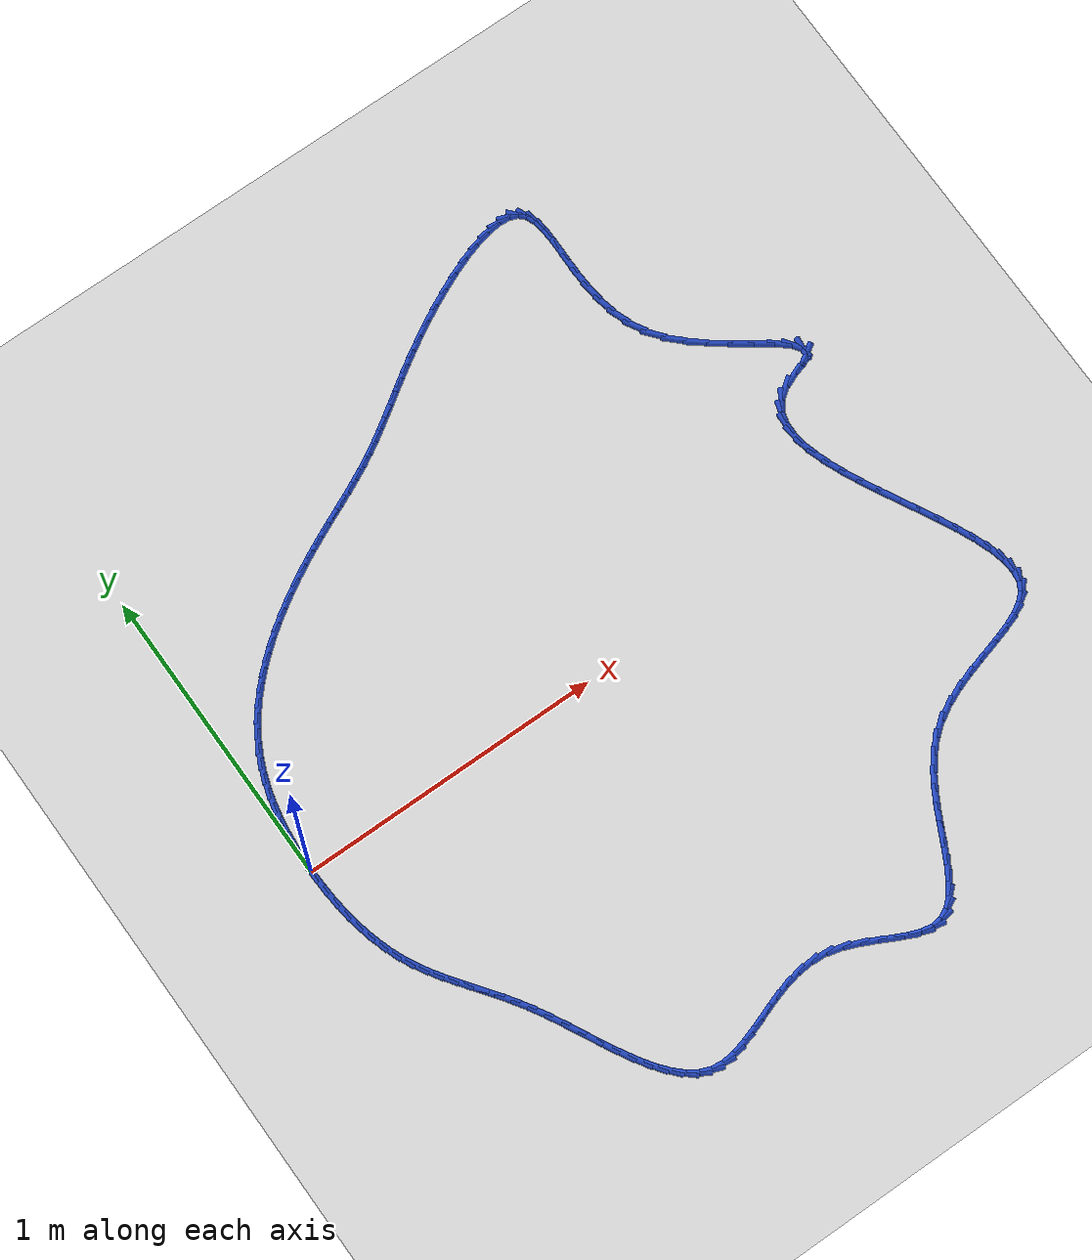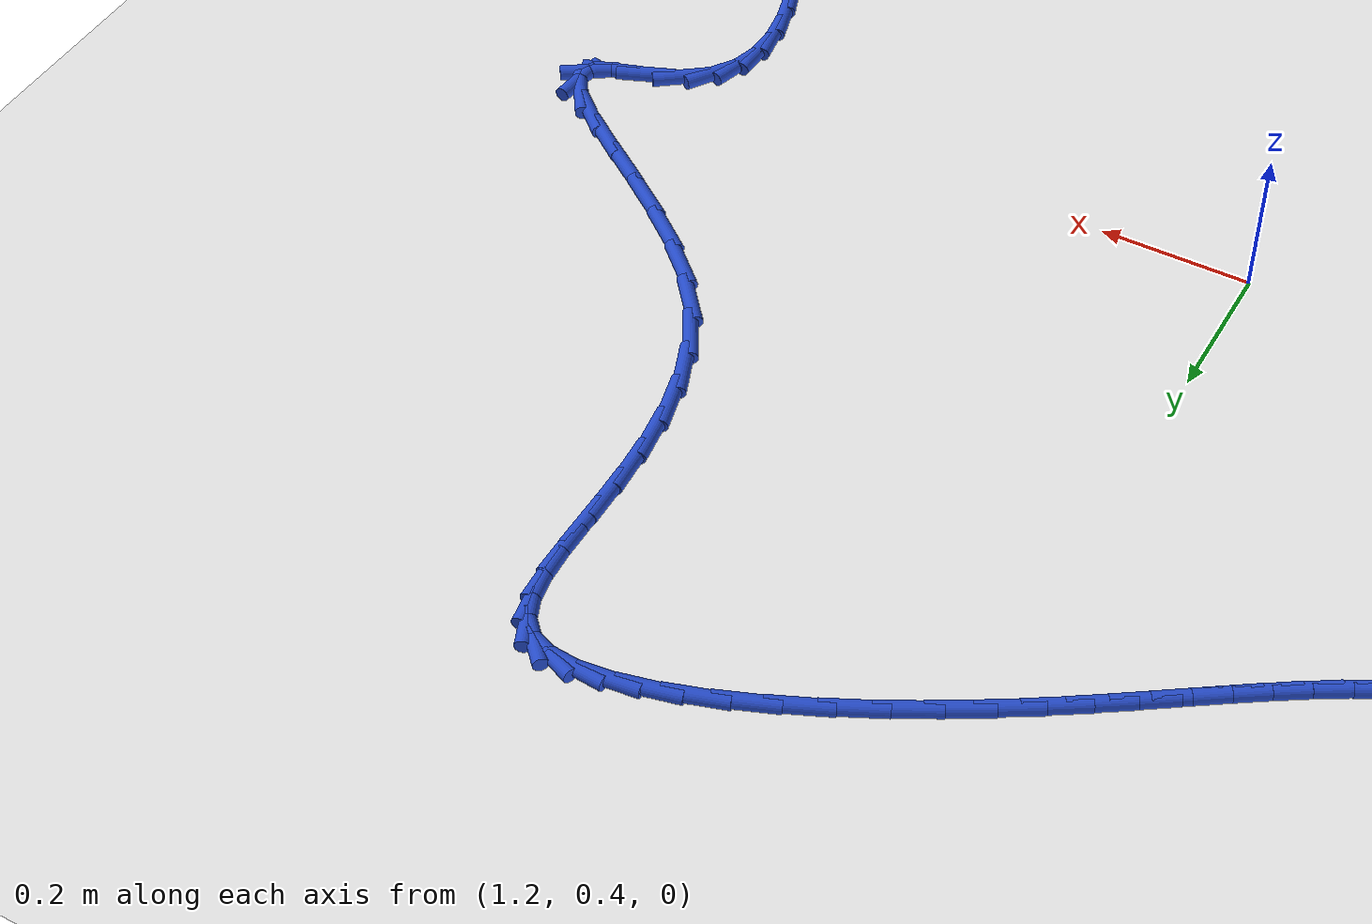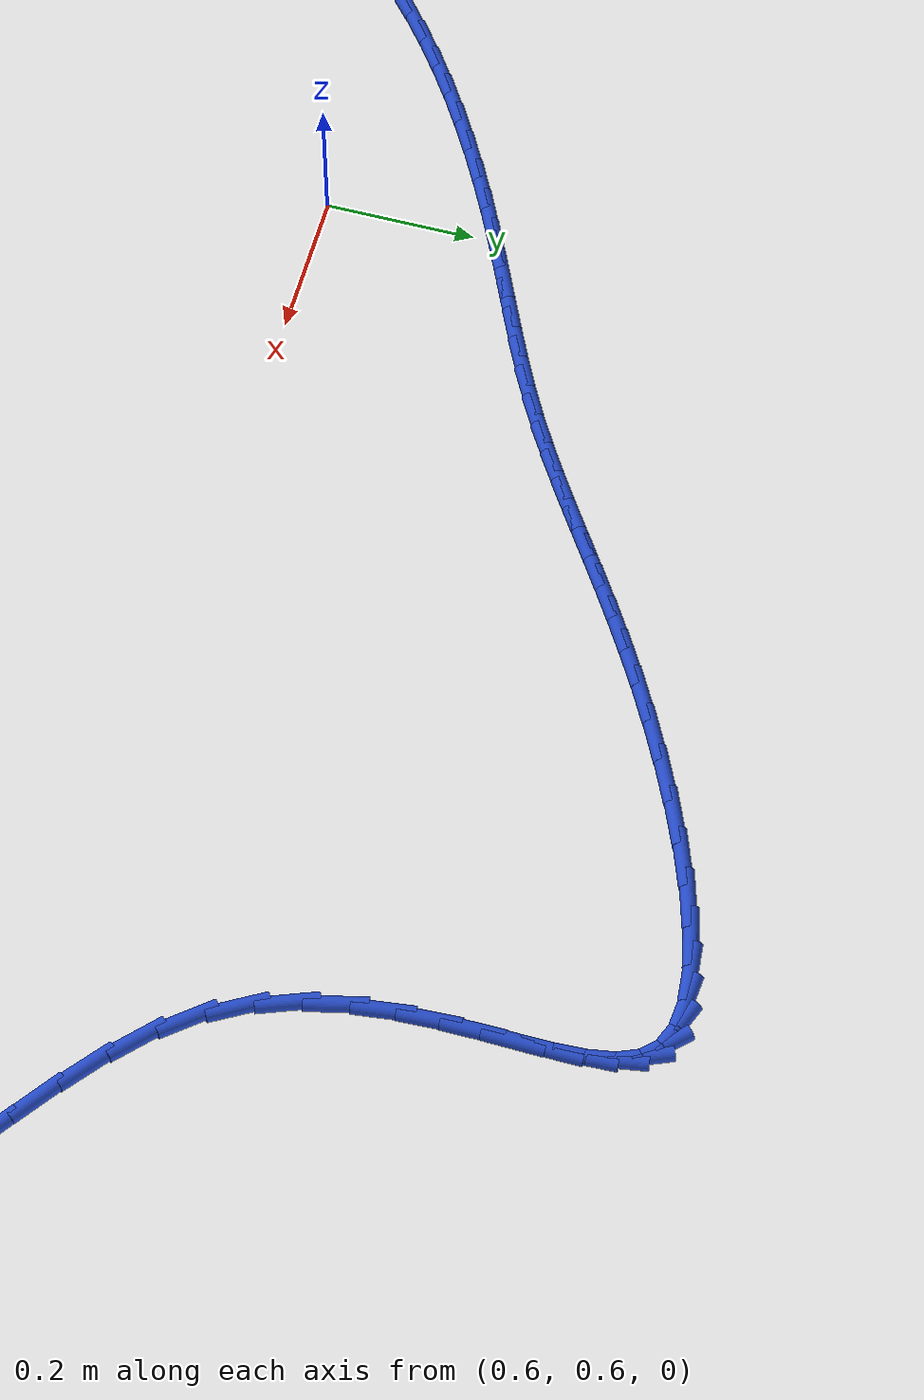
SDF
<sdf version="1.6">
 <world name="default">
  <light name="sun" type="directional">
   <pose>0 0 10 0 -0 0</pose>
   <diffuse>0.8 0.8 0.8 1</diffuse>
   <specular>0.2 0.2 0.2 1</specular>
   <attenuation>
    <range>1000</range>
    <constant>0.9</constant>
    <linear>0.01</linear>
    <quadratic>0.001</quadratic>
   </attenuation>
   <direction>-0.5 0.1 -0.9</direction>
  </light>
  <model name="ground_plane">
   <static>1</static>
   <link name="link">
    <collision name="collision">
     <geometry><plane><normal>0 0 1</normal><size>100 100</size></plane></geometry>
     <surface><friction><ode><mu>100</mu><mu2>50</mu2></ode></friction></surface>
    </collision>
    <visual name="visual">
     <cast_shadows>0</cast_shadows>
     <geometry><plane><normal>0 0 1</normal><size>100 100</size></plane></geometry>
     <material>
      <script><uri>file://media/materials/scripts/gazebo.material</uri><name>Gazebo/WhiteGlow</name></script>
     </material>
    </visual>
   </link>
  </model>
  <gravity>0 0 -9.8</gravity>
  <magnetic_field>6e-06 2.3e-05 -4.2e-05</magnetic_field>
  <atmosphere type="adiabatic"/>
  <physics name="default_physics" default="0" type="ode">
   <max_step_size>0.001</max_step_size>
   <real_time_factor>1</real_time_factor>
   <real_time_update_rate>1000</real_time_update_rate>
  </physics>
  <scene><ambient>0.4 0.4 0.4 1</ambient><background>0.7 0.7 0.7 1</background><shadows>1</shadows></scene>
  <spherical_coordinates>
   <surface_model>EARTH_WGS84</surface_model>
   <latitude_deg>0</latitude_deg>
   <longitude_deg>0</longitude_deg>
   <elevation>0</elevation>
   <heading_deg>0</heading_deg>
  </spherical_coordinates>
  <model name="line">
   <link name="link_0">
    <pose>1.8214596497756474e-17 1.3877787807814457e-17 0.01 0 1.57 1.5548178268451183</pose>
    <collision name="collision">
     <geometry><cylinder><radius>0.01</radius><length>0.08</length></cylinder></geometry>
    </collision>
    <visual name="visual">
     <material>
      <script><name>Gazebo/Blue</name><uri>file://media/materials/scripts/gazebo.material</uri></script>
     </material>
     <geometry><cylinder><radius>0.01</radius><length>0.08</length></cylinder></geometry>
    </visual>
   </link>
   <link name="link_1">
    <pose>0.0007842515850210458 0.04907750059657804 0.01 0 1.57 1.5136349057976526</pose>
    <collision name="collision">
     <geometry><cylinder><radius>0.01</radius><length>0.08</length></cylinder></geometry>
    </collision>
    <visual name="visual">
     <material>
      <script><name>Gazebo/Blue</name><uri>file://media/materials/scripts/gazebo.material</uri></script>
     </material>
     <geometry><cylinder><radius>0.01</radius><length>0.08</length></cylinder></geometry>
    </visual>
   </link>
   <link name="link_2">
    <pose>0.003576023252500154 0.09786443273712372 0.01 0 1.57 1.468387888100045</pose>
    <collision name="collision">
     <geometry><cylinder><radius>0.01</radius><length>0.08</length></cylinder></geometry>
    </collision>
    <visual name="visual">
     <material>
      <script><name>Gazebo/Blue</name><uri>file://media/materials/scripts/gazebo.material</uri></script>
     </material>
     <geometry><cylinder><radius>0.01</radius><length>0.08</length></cylinder></geometry>
    </visual>
   </link>
   <link name="link_3">
    <pose>0.008539704421732526 0.14616432779783262 0.01 0 1.57 1.4186726149800124</pose>
    <collision name="collision">
     <geometry><cylinder><radius>0.01</radius><length>0.08</length></cylinder></geometry>
    </collision>
    <visual name="visual">
     <material>
      <script><name>Gazebo/Blue</name><uri>file://media/materials/scripts/gazebo.material</uri></script>
     </material>
     <geometry><cylinder><radius>0.01</radius><length>0.08</length></cylinder></geometry>
    </visual>
   </link>
   <link name="link_4">
    <pose>0.015839684512013324 0.19378071715490022 0.01 0 1.57 1.3640906138248614</pose>
    <collision name="collision">
     <geometry><cylinder><radius>0.01</radius><length>0.08</length></cylinder></geometry>
    </collision>
    <visual name="visual">
     <material>
      <script><name>Gazebo/Blue</name><uri>file://media/materials/scripts/gazebo.material</uri></script>
     </material>
     <geometry><cylinder><radius>0.01</radius><length>0.08</length></cylinder></geometry>
    </visual>
   </link>
   <link name="link_5">
    <pose>0.02564035294263773 0.240517132184522 0.01 0 1.57 1.30427875366741</pose>
    <collision name="collision">
     <geometry><cylinder><radius>0.01</radius><length>0.08</length></cylinder></geometry>
    </collision>
    <visual name="visual">
     <material>
      <script><name>Gazebo/Blue</name><uri>file://media/materials/scripts/gazebo.material</uri></script>
     </material>
     <geometry><cylinder><radius>0.01</radius><length>0.08</length></cylinder></geometry>
    </visual>
   </link>
   <link name="link_6">
    <pose>0.03810609913290093 0.2861771042628936 0.01 0 1.57 1.2389517060004942</pose>
    <collision name="collision">
     <geometry><cylinder><radius>0.01</radius><length>0.08</length></cylinder></geometry>
    </collision>
    <visual name="visual">
     <material>
      <script><name>Gazebo/Blue</name><uri>file://media/materials/scripts/gazebo.material</uri></script>
     </material>
     <geometry><cylinder><radius>0.01</radius><length>0.08</length></cylinder></geometry>
    </visual>
   </link>
   <link name="link_7">
    <pose>0.05340131250209809 0.33056416476621037 0.01 0 1.57 1.1679579282214492</pose>
    <collision name="collision">
     <geometry><cylinder><radius>0.01</radius><length>0.08</length></cylinder></geometry>
    </collision>
    <visual name="visual">
     <material>
      <script><name>Gazebo/Blue</name><uri>file://media/materials/scripts/gazebo.material</uri></script>
     </material>
     <geometry><cylinder><radius>0.01</radius><length>0.08</length></cylinder></geometry>
    </visual>
   </link>
   <link name="link_8">
    <pose>0.07169038246952437 0.37348184507066806 0.01 0 1.57 1.0921105278431147</pose>
    <collision name="collision">
     <geometry><cylinder><radius>0.01</radius><length>0.08</length></cylinder></geometry>
    </collision>
    <visual name="visual">
     <material>
      <script><name>Gazebo/Blue</name><uri>file://media/materials/scripts/gazebo.material</uri></script>
     </material>
     <geometry><cylinder><radius>0.01</radius><length>0.08</length></cylinder></geometry>
    </visual>
   </link>
   <link name="link_9">
    <pose>0.09310748259988162 0.4147525787857607 0.01 0 1.57 1.0177618828842996</pose>
    <collision name="collision">
     <geometry><cylinder><radius>0.01</radius><length>0.08</length></cylinder></geometry>
    </collision>
    <visual name="visual">
     <material>
      <script><name>Gazebo/Blue</name><uri>file://media/materials/scripts/gazebo.material</uri></script>
     </material>
     <geometry><cylinder><radius>0.01</radius><length>0.08</length></cylinder></geometry>
    </visual>
   </link>
   <link name="link_10">
    <pose>0.1175489916067212 0.4543475576419809 0.01 0 1.57 0.948197487847134</pose>
    <collision name="collision">
     <geometry><cylinder><radius>0.01</radius><length>0.08</length></cylinder></geometry>
    </collision>
    <visual name="visual">
     <material>
      <script><name>Gazebo/Blue</name><uri>file://media/materials/scripts/gazebo.material</uri></script>
     </material>
     <geometry><cylinder><radius>0.01</radius><length>0.08</length></cylinder></geometry>
    </visual>
   </link>
   <link name="link_11">
    <pose>0.14479876541814232 0.49230836462536093 0.01 0 1.57 0.8836673601684549</pose>
    <collision name="collision">
     <geometry><cylinder><radius>0.01</radius><length>0.08</length></cylinder></geometry>
    </collision>
    <visual name="visual">
     <material>
      <script><name>Gazebo/Blue</name><uri>file://media/materials/scripts/gazebo.material</uri></script>
     </material>
     <geometry><cylinder><radius>0.01</radius><length>0.08</length></cylinder></geometry>
    </visual>
   </link>
   <link name="link_12">
    <pose>0.17463998865264915 0.5286770026753236 0.01 0 1.57 0.8242037764306432</pose>
    <collision name="collision">
     <geometry><cylinder><radius>0.01</radius><length>0.08</length></cylinder></geometry>
    </collision>
    <visual name="visual">
     <material>
      <script><name>Gazebo/Blue</name><uri>file://media/materials/scripts/gazebo.material</uri></script>
     </material>
     <geometry><cylinder><radius>0.01</radius><length>0.08</length></cylinder></geometry>
    </visual>
   </link>
   <link name="link_13">
    <pose>0.20685584592874584 0.5634954747312914 0.01 0 1.57 0.7696886944714623</pose>
    <collision name="collision">
     <geometry><cylinder><radius>0.01</radius><length>0.08</length></cylinder></geometry>
    </collision>
    <visual name="visual">
     <material>
      <script><name>Gazebo/Blue</name><uri>file://media/materials/scripts/gazebo.material</uri></script>
     </material>
     <geometry><cylinder><radius>0.01</radius><length>0.08</length></cylinder></geometry>
    </visual>
   </link>
   <link name="link_14">
    <pose>0.2412295218649367 0.5968057837326871 0.01 0 1.57 0.7199020837492931</pose>
    <collision name="collision">
     <geometry><cylinder><radius>0.01</radius><length>0.08</length></cylinder></geometry>
    </collision>
    <visual name="visual">
     <material>
      <script><name>Gazebo/Blue</name><uri>file://media/materials/scripts/gazebo.material</uri></script>
     </material>
     <geometry><cylinder><radius>0.01</radius><length>0.08</length></cylinder></geometry>
    </visual>
   </link>
   <link name="link_15">
    <pose>0.2775442010797258 0.6286499326189332 0.01 0 1.57 0.6745629541881316</pose>
    <collision name="collision">
     <geometry><cylinder><radius>0.01</radius><length>0.08</length></cylinder></geometry>
    </collision>
    <visual name="visual">
     <material>
      <script><name>Gazebo/Blue</name><uri>file://media/materials/scripts/gazebo.material</uri></script>
     </material>
     <geometry><cylinder><radius>0.01</radius><length>0.08</length></cylinder></geometry>
    </visual>
   </link>
   <link name="link_16">
    <pose>0.3155830681916175 0.6590699243294528 0.01 0 1.57 0.6333612831008195</pose>
    <collision name="collision">
     <geometry><cylinder><radius>0.01</radius><length>0.08</length></cylinder></geometry>
    </collision>
    <visual name="visual">
     <material>
      <script><name>Gazebo/Blue</name><uri>file://media/materials/scripts/gazebo.material</uri></script>
     </material>
     <geometry><cylinder><radius>0.01</radius><length>0.08</length></cylinder></geometry>
    </visual>
   </link>
   <link name="link_17">
    <pose>0.3551293078191161 0.6881077618036684 0.01 0 1.57 0.5959811809001965</pose>
    <collision name="collision">
     <geometry><cylinder><radius>0.01</radius><length>0.08</length></cylinder></geometry>
    </collision>
    <visual name="visual">
     <material>
      <script><name>Gazebo/Blue</name><uri>file://media/materials/scripts/gazebo.material</uri></script>
     </material>
     <geometry><cylinder><radius>0.01</radius><length>0.08</length></cylinder></geometry>
    </visual>
   </link>
   <link name="link_18">
    <pose>0.39596610458072545 0.7158054479810023 0.01 0 1.57 0.5621166843402141</pose>
    <collision name="collision">
     <geometry><cylinder><radius>0.01</radius><length>0.08</length></cylinder></geometry>
    </collision>
    <visual name="visual">
     <material>
      <script><name>Gazebo/Blue</name><uri>file://media/materials/scripts/gazebo.material</uri></script>
     </material>
     <geometry><cylinder><radius>0.01</radius><length>0.08</length></cylinder></geometry>
    </visual>
   </link>
   <link name="link_19">
    <pose>0.43787664309495017 0.7422049858008779 0.01 0 1.57 0.5314818775183597</pose>
    <collision name="collision">
     <geometry><cylinder><radius>0.01</radius><length>0.08</length></cylinder></geometry>
    </collision>
    <visual name="visual">
     <material>
      <script><name>Gazebo/Blue</name><uri>file://media/materials/scripts/gazebo.material</uri></script>
     </material>
     <geometry><cylinder><radius>0.01</radius><length>0.08</length></cylinder></geometry>
    </visual>
   </link>
   <link name="link_20">
    <pose>0.480644107980294 0.7673483782027171 0.01 0 1.57 0.5038169510047724</pose>
    <collision name="collision">
     <geometry><cylinder><radius>0.01</radius><length>0.08</length></cylinder></geometry>
    </collision>
    <visual name="visual">
     <material>
      <script><name>Gazebo/Blue</name><uri>file://media/materials/scripts/gazebo.material</uri></script>
     </material>
     <geometry><cylinder><radius>0.01</radius><length>0.08</length></cylinder></geometry>
    </visual>
   </link>
   <link name="link_21">
    <pose>0.5240516838552616 0.791277628125943 0.01 0 1.57 0.4788915536792407</pose>
    <collision name="collision">
     <geometry><cylinder><radius>0.01</radius><length>0.08</length></cylinder></geometry>
    </collision>
    <visual name="visual">
     <material>
      <script><name>Gazebo/Blue</name><uri>file://media/materials/scripts/gazebo.material</uri></script>
     </material>
     <geometry><cylinder><radius>0.01</radius><length>0.08</length></cylinder></geometry>
    </visual>
   </link>
   <link name="link_22">
    <pose>0.5678825553383569 0.8140347385099787 0.01 0 1.57 0.4570493568227514</pose>
    <collision name="collision">
     <geometry><cylinder><radius>0.01</radius><length>0.08</length></cylinder></geometry>
    </collision>
    <visual name="visual">
     <material>
      <script><name>Gazebo/Blue</name><uri>file://media/materials/scripts/gazebo.material</uri></script>
     </material>
     <geometry><cylinder><radius>0.01</radius><length>0.08</length></cylinder></geometry>
    </visual>
   </link>
   <link name="link_23">
    <pose>0.6119143527583014 0.8356886600461111 0.01 0 1.57 0.4420971581341277</pose>
    <collision name="collision">
     <geometry><cylinder><radius>0.01</radius><length>0.08</length></cylinder></geometry>
    </collision>
    <visual name="visual">
     <material>
      <script><name>Gazebo/Blue</name><uri>file://media/materials/scripts/gazebo.material</uri></script>
     </material>
     <geometry><cylinder><radius>0.01</radius><length>0.08</length></cylinder></geometry>
    </visual>
   </link>
   <link name="link_24">
    <pose>0.6558848197423763 0.856501861764612 0.01 0 1.57 0.43585741994843274</pose>
    <collision name="collision">
     <geometry><cylinder><radius>0.01</radius><length>0.08</length></cylinder></geometry>
    </collision>
    <visual name="visual">
     <material>
      <script><name>Gazebo/Blue</name><uri>file://media/materials/scripts/gazebo.material</uri></script>
     </material>
     <geometry><cylinder><radius>0.01</radius><length>0.08</length></cylinder></geometry>
    </visual>
   </link>
   <link name="link_25">
    <pose>0.6995142677260668 0.8768213884736384 0.01 0 1.57 0.43858317244320516</pose>
    <collision name="collision">
     <geometry><cylinder><radius>0.01</radius><length>0.08</length></cylinder></geometry>
    </collision>
    <visual name="visual">
     <material>
      <script><name>Gazebo/Blue</name><uri>file://media/materials/scripts/gazebo.material</uri></script>
     </material>
     <geometry><cylinder><radius>0.01</radius><length>0.08</length></cylinder></geometry>
    </visual>
   </link>
   <link name="link_26">
    <pose>0.7425229350188614 0.8969946397668027 0.01 0 1.57 0.4506512488615498</pose>
    <collision name="collision">
     <geometry><cylinder><radius>0.01</radius><length>0.08</length></cylinder></geometry>
    </collision>
    <visual name="visual">
     <material>
      <script><name>Gazebo/Blue</name><uri>file://media/materials/scripts/gazebo.material</uri></script>
     </material>
     <geometry><cylinder><radius>0.01</radius><length>0.08</length></cylinder></geometry>
    </visual>
   </link>
   <link name="link_27">
    <pose>0.7846310599302466 0.9173690152377156 0.01 0 1.57 0.4725789795757197</pose>
    <collision name="collision">
     <geometry><cylinder><radius>0.01</radius><length>0.08</length></cylinder></geometry>
    </collision>
    <visual name="visual">
     <material>
      <script><name>Gazebo/Blue</name><uri>file://media/materials/scripts/gazebo.material</uri></script>
     </material>
     <geometry><cylinder><radius>0.01</radius><length>0.08</length></cylinder></geometry>
    </visual>
   </link>
   <link name="link_28">
    <pose>0.8255588807697106 0.9382919144799886 0.01 0 1.57 0.5044726837128017</pose>
    <collision name="collision">
     <geometry><cylinder><radius>0.01</radius><length>0.08</length></cylinder></geometry>
    </collision>
    <visual name="visual">
     <material>
      <script><name>Gazebo/Blue</name><uri>file://media/materials/scripts/gazebo.material</uri></script>
     </material>
     <geometry><cylinder><radius>0.01</radius><length>0.08</length></cylinder></geometry>
    </visual>
   </link>
   <link name="link_29">
    <pose>0.8650518140848992 0.9600969224044723 0.01 0 1.57 0.5377605878193324</pose>
    <collision name="collision">
     <geometry><cylinder><radius>0.01</radius><length>0.08</length></cylinder></geometry>
    </collision>
    <visual name="visual">
     <material>
      <script><name>Gazebo/Blue</name><uri>file://media/materials/scripts/gazebo.material</uri></script>
     </material>
     <geometry><cylinder><radius>0.01</radius><length>0.08</length></cylinder></geometry>
    </visual>
   </link>
   <link name="link_30">
    <pose>0.9032701948146044 0.9828899683605195 0.01 0 1.57 0.5642962442708688</pose>
    <collision name="collision">
     <geometry><cylinder><radius>0.01</radius><length>0.08</length></cylinder></geometry>
    </collision>
    <visual name="visual">
     <material>
      <script><name>Gazebo/Blue</name><uri>file://media/materials/scripts/gazebo.material</uri></script>
     </material>
     <geometry><cylinder><radius>0.01</radius><length>0.08</length></cylinder></geometry>
    </visual>
   </link>
   <link name="link_31">
    <pose>0.9407144890048875 1.0065903600874022 0.01 0 1.57 0.5830407878742155</pose>
    <collision name="collision">
     <geometry><cylinder><radius>0.01</radius><length>0.08</length></cylinder></geometry>
    </collision>
    <visual name="visual">
     <material>
      <script><name>Gazebo/Blue</name><uri>file://media/materials/scripts/gazebo.material</uri></script>
     </material>
     <geometry><cylinder><radius>0.01</radius><length>0.08</length></cylinder></geometry>
    </visual>
   </link>
   <link name="link_32">
    <pose>0.9778951980221898 1.0311118991898245 0.01 0 1.57 0.5936182516509998</pose>
    <collision name="collision">
     <geometry><cylinder><radius>0.01</radius><length>0.08</length></cylinder></geometry>
    </collision>
    <visual name="visual">
     <material>
      <script><name>Gazebo/Blue</name><uri>file://media/materials/scripts/gazebo.material</uri></script>
     </material>
     <geometry><cylinder><radius>0.01</radius><length>0.08</length></cylinder></geometry>
    </visual>
   </link>
   <link name="link_33">
    <pose>1.0153228232329512 1.0563683872724916 0.01 0 1.57 0.5960908205367755</pose>
    <collision name="collision">
     <geometry><cylinder><radius>0.01</radius><length>0.08</length></cylinder></geometry>
    </collision>
    <visual name="visual">
     <material>
      <script><name>Gazebo/Blue</name><uri>file://media/materials/scripts/gazebo.material</uri></script>
     </material>
     <geometry><cylinder><radius>0.01</radius><length>0.08</length></cylinder></geometry>
    </visual>
   </link>
   <link name="link_34">
    <pose>1.0535078660036135 1.0822736259401078 0.01 0 1.57 0.5909066540324872</pose>
    <collision name="collision">
     <geometry><cylinder><radius>0.01</radius><length>0.08</length></cylinder></geometry>
    </collision>
    <visual name="visual">
     <material>
      <script><name>Gazebo/Blue</name><uri>file://media/materials/scripts/gazebo.material</uri></script>
     </material>
     <geometry><cylinder><radius>0.01</radius><length>0.08</length></cylinder></geometry>
    </visual>
   </link>
   <link name="link_35">
    <pose>1.0929608277006175 1.108741416797379 0.01 0 1.57 0.5788221673163818</pose>
    <collision name="collision">
     <geometry><cylinder><radius>0.01</radius><length>0.08</length></cylinder></geometry>
    </collision>
    <visual name="visual">
     <material>
      <script><name>Gazebo/Blue</name><uri>file://media/materials/scripts/gazebo.material</uri></script>
     </material>
     <geometry><cylinder><radius>0.01</radius><length>0.08</length></cylinder></geometry>
    </visual>
   </link>
   <link name="link_36">
    <pose>1.1341922096904038 1.1356855614490087 0.01 0 1.57 0.5608121976195135</pose>
    <collision name="collision">
     <geometry><cylinder><radius>0.01</radius><length>0.08</length></cylinder></geometry>
    </collision>
    <visual name="visual">
     <material>
      <script><name>Gazebo/Blue</name><uri>file://media/materials/scripts/gazebo.material</uri></script>
     </material>
     <geometry><cylinder><radius>0.01</radius><length>0.08</length></cylinder></geometry>
    </visual>
   </link>
   <link name="link_37">
    <pose>1.1777125133394137 1.163019861499702 0.01 0 1.57 0.5379779724539197</pose>
    <collision name="collision">
     <geometry><cylinder><radius>0.01</radius><length>0.08</length></cylinder></geometry>
    </collision>
    <visual name="visual">
     <material>
      <script><name>Gazebo/Blue</name><uri>file://media/materials/scripts/gazebo.material</uri></script>
     </material>
     <geometry><cylinder><radius>0.01</radius><length>0.08</length></cylinder></geometry>
    </visual>
   </link>
   <link name="link_38">
    <pose>1.224032240014088 1.190658118554164 0.01 0 1.57 0.511590260849804</pose>
    <collision name="collision">
     <geometry><cylinder><radius>0.01</radius><length>0.08</length></cylinder></geometry>
    </collision>
    <visual name="visual">
     <material>
      <script><name>Gazebo/Blue</name><uri>file://media/materials/scripts/gazebo.material</uri></script>
     </material>
     <geometry><cylinder><radius>0.01</radius><length>0.08</length></cylinder></geometry>
    </visual>
   </link>
   <link name="link_39">
    <pose>1.2735407798031957 1.2184546090722577 0.01 0 1.57 0.4830601614089095</pose>
    <collision name="collision">
     <geometry><cylinder><radius>0.01</radius><length>0.08</length></cylinder></geometry>
    </collision>
    <visual name="visual">
     <material>
      <script><name>Gazebo/Blue</name><uri>file://media/materials/scripts/gazebo.material</uri></script>
     </material>
     <geometry><cylinder><radius>0.01</radius><length>0.08</length></cylinder></geometry>
    </visual>
   </link>
   <link name="link_40">
    <pose>1.325556849074618 1.2457373826459686 0.01 0 1.57 0.45127121917177127</pose>
    <collision name="collision">
     <geometry><cylinder><radius>0.01</radius><length>0.08</length></cylinder></geometry>
    </collision>
    <visual name="visual">
     <material>
      <script><name>Gazebo/Blue</name><uri>file://media/materials/scripts/gazebo.material</uri></script>
     </material>
     <geometry><cylinder><radius>0.01</radius><length>0.08</length></cylinder></geometry>
    </visual>
   </link>
   <link name="link_41">
    <pose>1.3788407832566785 1.27156004946789 0.01 0 1.57 0.41385574941185355</pose>
    <collision name="collision">
     <geometry><cylinder><radius>0.01</radius><length>0.08</length></cylinder></geometry>
    </collision>
    <visual name="visual">
     <material>
      <script><name>Gazebo/Blue</name><uri>file://media/materials/scripts/gazebo.material</uri></script>
     </material>
     <geometry><cylinder><radius>0.01</radius><length>0.08</length></cylinder></geometry>
    </visual>
   </link>
   <link name="link_42">
    <pose>1.43214808698638 1.2949738454384878 0.01 0 1.57 0.3675587106381804</pose>
    <collision name="collision">
     <geometry><cylinder><radius>0.01</radius><length>0.08</length></cylinder></geometry>
    </collision>
    <visual name="visual">
     <material>
      <script><name>Gazebo/Blue</name><uri>file://media/materials/scripts/gazebo.material</uri></script>
     </material>
     <geometry><cylinder><radius>0.01</radius><length>0.08</length></cylinder></geometry>
    </visual>
   </link>
   <link name="link_43">
    <pose>1.484234264900728 1.3150300064582292 0.01 0 1.57 0.3073462885753097</pose>
    <collision name="collision">
     <geometry><cylinder><radius>0.01</radius><length>0.08</length></cylinder></geometry>
    </collision>
    <visual name="visual">
     <material>
      <script><name>Gazebo/Blue</name><uri>file://media/materials/scripts/gazebo.material</uri></script>
     </material>
     <geometry><cylinder><radius>0.01</radius><length>0.08</length></cylinder></geometry>
    </visual>
   </link>
   <link name="link_44">
    <pose>1.533854821636727 1.330779768427581 0.01 0 1.57 0.2247273955039373</pose>
    <collision name="collision">
     <geometry><cylinder><radius>0.01</radius><length>0.08</length></cylinder></geometry>
    </collision>
    <visual name="visual">
     <material>
      <script><name>Gazebo/Blue</name><uri>file://media/materials/scripts/gazebo.material</uri></script>
     </material>
     <geometry><cylinder><radius>0.01</radius><length>0.08</length></cylinder></geometry>
    </visual>
   </link>
   <link name="link_45">
    <pose>1.57976526183138 1.3412743672470098 0.01 0 1.57 0.10438262588103439</pose>
    <collision name="collision">
     <geometry><cylinder><radius>0.01</radius><length>0.08</length></cylinder></geometry>
    </collision>
    <visual name="visual">
     <material>
      <script><name>Gazebo/Blue</name><uri>file://media/materials/scripts/gazebo.material</uri></script>
     </material>
     <geometry><cylinder><radius>0.01</radius><length>0.08</length></cylinder></geometry>
    </visual>
   </link>
   <link name="link_46">
    <pose>1.6207210901216926 1.3455650388169822 0.01 0 1.57 -0.08215899414609175</pose>
    <collision name="collision">
     <geometry><cylinder><radius>0.01</radius><length>0.08</length></cylinder></geometry>
    </collision>
    <visual name="visual">
     <material>
      <script><name>Gazebo/Blue</name><uri>file://media/materials/scripts/gazebo.material</uri></script>
     </material>
     <geometry><cylinder><radius>0.01</radius><length>0.08</length></cylinder></geometry>
    </visual>
   </link>
   <link name="link_47">
    <pose>1.6554778111446682 1.342703019037965 0.01 0 1.57 -0.3817123597840885</pose>
    <collision name="collision">
     <geometry><cylinder><radius>0.01</radius><length>0.08</length></cylinder></geometry>
    </collision>
    <visual name="visual">
     <material>
      <script><name>Gazebo/Blue</name><uri>file://media/materials/scripts/gazebo.material</uri></script>
     </material>
     <geometry><cylinder><radius>0.01</radius><length>0.08</length></cylinder></geometry>
    </visual>
   </link>
   <link name="link_48">
    <pose>1.6827909295373105 1.3317395438104245 0.01 0 1.57 -0.80663547609478</pose>
    <collision name="collision">
     <geometry><cylinder><radius>0.01</radius><length>0.08</length></cylinder></geometry>
    </collision>
    <visual name="visual">
     <material>
      <script><name>Gazebo/Blue</name><uri>file://media/materials/scripts/gazebo.material</uri></script>
     </material>
     <geometry><cylinder><radius>0.01</radius><length>0.08</length></cylinder></geometry>
    </visual>
   </link>
   <link name="link_49">
    <pose>1.7017529687783328 1.3119544968479397 0.01 0 1.57 -1.1778031978639705</pose>
    <collision name="collision">
     <geometry><cylinder><radius>0.01</radius><length>0.08</length></cylinder></geometry>
    </collision>
    <visual name="visual">
     <material>
      <script><name>Gazebo/Blue</name><uri>file://media/materials/scripts/gazebo.material</uri></script>
     </material>
     <geometry><cylinder><radius>0.01</radius><length>0.08</length></cylinder></geometry>
    </visual>
   </link>
   <link name="link_50">
    <pose>1.7133718825119197 1.2839272705689544 0.01 0 1.57 -1.403229055161632</pose>
    <collision name="collision">
     <geometry><cylinder><radius>0.01</radius><length>0.08</length></cylinder></geometry>
    </collision>
    <visual name="visual">
     <material>
      <script><name>Gazebo/Blue</name><uri>file://media/materials/scripts/gazebo.material</uri></script>
     </material>
     <geometry><cylinder><radius>0.01</radius><length>0.08</length></cylinder></geometry>
    </visual>
   </link>
   <link name="link_51">
    <pose>1.7193314168991185 1.2486957435712438 0.01 0 1.57 -1.5228912177226923</pose>
    <collision name="collision">
     <geometry><cylinder><radius>0.01</radius><length>0.08</length></cylinder></geometry>
    </collision>
    <visual name="visual">
     <material>
      <script><name>Gazebo/Blue</name><uri>file://media/materials/scripts/gazebo.material</uri></script>
     </material>
     <geometry><cylinder><radius>0.01</radius><length>0.08</length></cylinder></geometry>
    </visual>
   </link>
   <link name="link_52">
    <pose>1.721316083719696 1.2072983138806535 0.01 0 1.57 1.564225988293905</pose>
    <collision name="collision">
     <geometry><cylinder><radius>0.01</radius><length>0.08</length></cylinder></geometry>
    </collision>
    <visual name="visual">
     <material>
      <script><name>Gazebo/Blue</name><uri>file://media/materials/scripts/gazebo.material</uri></script>
     </material>
     <geometry><cylinder><radius>0.01</radius><length>0.08</length></cylinder></geometry>
    </visual>
   </link>
   <link name="link_53">
    <pose>1.7210103947534194 1.1607733795230275 0.01 0 1.57 1.5527887853068787</pose>
    <collision name="collision">
     <geometry><cylinder><radius>0.01</radius><length>0.08</length></cylinder></geometry>
    </collision>
    <visual name="visual">
     <material>
      <script><name>Gazebo/Blue</name><uri>file://media/materials/scripts/gazebo.material</uri></script>
     </material>
     <geometry><cylinder><radius>0.01</radius><length>0.08</length></cylinder></geometry>
    </visual>
   </link>
   <link name="link_54">
    <pose>1.7200988617800568 1.1101593385242112 0.01 0 1.57 -1.5676819125818602</pose>
    <collision name="collision">
     <geometry><cylinder><radius>0.01</radius><length>0.08</length></cylinder></geometry>
    </collision>
    <visual name="visual">
     <material>
      <script><name>Gazebo/Blue</name><uri>file://media/materials/scripts/gazebo.material</uri></script>
     </material>
     <geometry><cylinder><radius>0.01</radius><length>0.08</length></cylinder></geometry>
    </visual>
   </link>
   <link name="link_55">
    <pose>1.7202659965793734 1.056494588910048 0.01 0 1.57 -1.5182142903779752</pose>
    <collision name="collision">
     <geometry><cylinder><radius>0.01</radius><length>0.08</length></cylinder></geometry>
    </collision>
    <visual name="visual">
     <material>
      <script><name>Gazebo/Blue</name><uri>file://media/materials/scripts/gazebo.material</uri></script>
     </material>
     <geometry><cylinder><radius>0.01</radius><length>0.08</length></cylinder></geometry>
    </visual>
   </link>
   <link name="link_56">
    <pose>1.7231963109311381 1.0008175287063832 0.01 0 1.57 -1.4412890853291829</pose>
    <collision name="collision">
     <geometry><cylinder><radius>0.01</radius><length>0.08</length></cylinder></geometry>
    </collision>
    <visual name="visual">
     <material>
      <script><name>Gazebo/Blue</name><uri>file://media/materials/scripts/gazebo.material</uri></script>
     </material>
     <geometry><cylinder><radius>0.01</radius><length>0.08</length></cylinder></geometry>
    </visual>
   </link>
   <link name="link_57">
    <pose>1.730574316615117 0.9441665559390618 0.01 0 1.57 -1.336430509997396</pose>
    <collision name="collision">
     <geometry><cylinder><radius>0.01</radius><length>0.08</length></cylinder></geometry>
    </collision>
    <visual name="visual">
     <material>
      <script><name>Gazebo/Blue</name><uri>file://media/materials/scripts/gazebo.material</uri></script>
     </material>
     <geometry><cylinder><radius>0.01</radius><length>0.08</length></cylinder></geometry>
    </visual>
   </link>
   <link name="link_58">
    <pose>1.7440845254110777 0.8875800686339272 0.01 0 1.57 -1.203825424232179</pose>
    <collision name="collision">
     <geometry><cylinder><radius>0.01</radius><length>0.08</length></cylinder></geometry>
    </collision>
    <visual name="visual">
     <material>
      <script><name>Gazebo/Blue</name><uri>file://media/materials/scripts/gazebo.material</uri></script>
     </material>
     <geometry><cylinder><radius>0.01</radius><length>0.08</length></cylinder></geometry>
    </visual>
   </link>
   <link name="link_59">
    <pose>1.7654114490987878 0.8320964648168258 0.01 0 1.57 -1.0467625526400808</pose>
    <collision name="collision">
     <geometry><cylinder><radius>0.01</radius><length>0.08</length></cylinder></geometry>
    </collision>
    <visual name="visual">
     <material>
      <script><name>Gazebo/Blue</name><uri>file://media/materials/scripts/gazebo.material</uri></script>
     </material>
     <geometry><cylinder><radius>0.01</radius><length>0.08</length></cylinder></geometry>
    </visual>
   </link>
   <link name="link_60">
    <pose>1.7962395994580127 0.7787541425136009 0.01 0 1.57 -0.8804024752165751</pose>
    <collision name="collision">
     <geometry><cylinder><radius>0.01</radius><length>0.08</length></cylinder></geometry>
    </collision>
    <visual name="visual">
     <material>
      <script><name>Gazebo/Blue</name><uri>file://media/materials/scripts/gazebo.material</uri></script>
     </material>
     <geometry><cylinder><radius>0.01</radius><length>0.08</length></cylinder></geometry>
    </visual>
   </link>
   <link name="link_61">
    <pose>1.8377466581048083 0.7285033722472357 0.01 0 1.57 -0.7547351194921746</pose>
    <collision name="collision">
     <geometry><cylinder><radius>0.01</radius><length>0.08</length></cylinder></geometry>
    </collision>
    <visual name="visual">
     <material>
      <script><name>Gazebo/Blue</name><uri>file://media/materials/scripts/gazebo.material</uri></script>
     </material>
     <geometry><cylinder><radius>0.01</radius><length>0.08</length></cylinder></geometry>
    </visual>
   </link>
   <link name="link_62">
    <pose>1.8875400843740928 0.6816736351780781 0.01 0 1.57 -0.6750035557961598</pose>
    <collision name="collision">
     <geometry><cylinder><radius>0.01</radius><length>0.08</length></cylinder></geometry>
    </collision>
    <visual name="visual">
     <material>
      <script><name>Gazebo/Blue</name><uri>file://media/materials/scripts/gazebo.material</uri></script>
     </material>
     <geometry><cylinder><radius>0.01</radius><length>0.08</length></cylinder></geometry>
    </visual>
   </link>
   <link name="link_63">
    <pose>1.9416933619311179 0.6383276851584 0.01 0 1.57 -0.6300580881630947</pose>
    <collision name="collision">
     <geometry><cylinder><radius>0.01</radius><length>0.08</length></cylinder></geometry>
    </collision>
    <visual name="visual">
     <material>
      <script><name>Gazebo/Blue</name><uri>file://media/materials/scripts/gazebo.material</uri></script>
     </material>
     <geometry><cylinder><radius>0.01</radius><length>0.08</length></cylinder></geometry>
    </visual>
   </link>
   <link name="link_64">
    <pose>1.996274049443884 0.5985272458034269 0.01 0 1.57 -0.616487457971596</pose>
    <collision name="collision">
     <geometry><cylinder><radius>0.01</radius><length>0.08</length></cylinder></geometry>
    </collision>
    <visual name="visual">
     <material>
      <script><name>Gazebo/Blue</name><uri>file://media/materials/scripts/gazebo.material</uri></script>
     </material>
     <geometry><cylinder><radius>0.01</radius><length>0.08</length></cylinder></geometry>
    </visual>
   </link>
   <link name="link_65">
    <pose>2.047349705580397 0.5623340407283828 0.01 0 1.57 -0.6404967627111215</pose>
    <collision name="collision">
     <geometry><cylinder><radius>0.01</radius><length>0.08</length></cylinder></geometry>
    </collision>
    <visual name="visual">
     <material>
      <script><name>Gazebo/Blue</name><uri>file://media/materials/scripts/gazebo.material</uri></script>
     </material>
     <geometry><cylinder><radius>0.01</radius><length>0.08</length></cylinder></geometry>
    </visual>
   </link>
   <link name="link_66">
    <pose>2.0909878890086606 0.5298097935484924 0.01 0 1.57 -0.728554793761495</pose>
    <collision name="collision">
     <geometry><cylinder><radius>0.01</radius><length>0.08</length></cylinder></geometry>
    </collision>
    <visual name="visual">
     <material>
      <script><name>Gazebo/Blue</name><uri>file://media/materials/scripts/gazebo.material</uri></script>
     </material>
     <geometry><cylinder><radius>0.01</radius><length>0.08</length></cylinder></geometry>
    </visual>
   </link>
   <link name="link_67">
    <pose>2.123256158396677 0.5010162278789809 0.01 0 1.57 -0.9745741588385918</pose>
    <collision name="collision">
     <geometry><cylinder><radius>0.01</radius><length>0.08</length></cylinder></geometry>
    </collision>
    <visual name="visual">
     <material>
      <script><name>Gazebo/Blue</name><uri>file://media/materials/scripts/gazebo.material</uri></script>
     </material>
     <geometry><cylinder><radius>0.01</radius><length>0.08</length></cylinder></geometry>
    </visual>
   </link>
   <link name="link_68">
    <pose>2.1402220724124508 0.4760150673350723 0.01 0 1.57 1.463914358564587</pose>
    <collision name="collision">
     <geometry><cylinder><radius>0.01</radius><length>0.08</length></cylinder></geometry>
    </collision>
    <visual name="visual">
     <material>
      <script><name>Gazebo/Blue</name><uri>file://media/materials/scripts/gazebo.material</uri></script>
     </material>
     <geometry><cylinder><radius>0.01</radius><length>0.08</length></cylinder></geometry>
    </visual>
   </link>
   <link name="link_69">
    <pose>2.137953189723986 0.4548680355319918 0.01 0 1.57 0.5963319760171646</pose>
    <collision name="collision">
     <geometry><cylinder><radius>0.01</radius><length>0.08</length></cylinder></geometry>
    </collision>
    <visual name="visual">
     <material>
      <script><name>Gazebo/Blue</name><uri>file://media/materials/scripts/gazebo.material</uri></script>
     </material>
     <geometry><cylinder><radius>0.01</radius><length>0.08</length></cylinder></geometry>
    </visual>
   </link>
   <link name="link_70">
    <pose>2.112554015069137 0.4376279534257839 0.01 0 1.57 0.32237474702535807</pose>
    <collision name="collision">
     <geometry><cylinder><radius>0.01</radius><length>0.08</length></cylinder></geometry>
    </collision>
    <visual name="visual">
     <material>
      <script><name>Gazebo/Blue</name><uri>file://media/materials/scripts/gazebo.material</uri></script>
     </material>
     <geometry><cylinder><radius>0.01</radius><length>0.08</length></cylinder></geometry>
    </visual>
   </link>
   <link name="link_71">
    <pose>2.067487507717609 0.422574522042555 0.01 0 1.57 0.386333498994581</pose>
    <collision name="collision">
     <geometry><cylinder><radius>0.01</radius><length>0.08</length></cylinder></geometry>
    </collision>
    <visual name="visual">
     <material>
      <script><name>Gazebo/Blue</name><uri>file://media/materials/scripts/gazebo.material</uri></script>
     </material>
     <geometry><cylinder><radius>0.01</radius><length>0.08</length></cylinder></geometry>
    </visual>
   </link>
   <link name="link_72">
    <pose>2.022192600917155 0.4041496713660784 0.01 0 1.57 0.6477388447219717</pose>
    <collision name="collision">
     <geometry><cylinder><radius>0.01</radius><length>0.08</length></cylinder></geometry>
    </collision>
    <visual name="visual">
     <material>
      <script><name>Gazebo/Blue</name><uri>file://media/materials/scripts/gazebo.material</uri></script>
     </material>
     <geometry><cylinder><radius>0.01</radius><length>0.08</length></cylinder></geometry>
    </visual>
   </link>
   <link name="link_73">
    <pose>1.9889856657466016 0.3790238891228696 0.01 0 1.57 0.972353337092278</pose>
    <collision name="collision">
     <geometry><cylinder><radius>0.01</radius><length>0.08</length></cylinder></geometry>
    </collision>
    <visual name="visual">
     <material>
      <script><name>Gazebo/Blue</name><uri>file://media/materials/scripts/gazebo.material</uri></script>
     </material>
     <geometry><cylinder><radius>0.01</radius><length>0.08</length></cylinder></geometry>
    </visual>
   </link>
   <link name="link_74">
    <pose>1.9675628898797555 0.3476054444227995 0.01 0 1.57 1.2859220008578158</pose>
    <collision name="collision">
     <geometry><cylinder><radius>0.01</radius><length>0.08</length></cylinder></geometry>
    </collision>
    <visual name="visual">
     <material>
      <script><name>Gazebo/Blue</name><uri>file://media/materials/scripts/gazebo.material</uri></script>
     </material>
     <geometry><cylinder><radius>0.01</radius><length>0.08</length></cylinder></geometry>
    </visual>
   </link>
   <link name="link_75">
    <pose>1.9567174759545785 0.3105700478659384 0.01 0 1.57 1.5356757695892835</pose>
    <collision name="collision">
     <geometry><cylinder><radius>0.01</radius><length>0.08</length></cylinder></geometry>
    </collision>
    <visual name="visual">
     <material>
      <script><name>Gazebo/Blue</name><uri>file://media/materials/scripts/gazebo.material</uri></script>
     </material>
     <geometry><cylinder><radius>0.01</radius><length>0.08</length></cylinder></geometry>
    </visual>
   </link>
   <link name="link_76">
    <pose>1.9552426266090301 0.26859341005235626 0.01 0 1.57 -1.427142964782407</pose>
    <collision name="collision">
     <geometry><cylinder><radius>0.01</radius><length>0.08</length></cylinder></geometry>
    </collision>
    <visual name="visual">
     <material>
      <script><name>Gazebo/Blue</name><uri>file://media/materials/scripts/gazebo.material</uri></script>
     </material>
     <geometry><cylinder><radius>0.01</radius><length>0.08</length></cylinder></geometry>
    </visual>
   </link>
   <link name="link_77">
    <pose>1.9619315444810725 0.22235124158212408 0.01 0 1.57 -1.3035108197939442</pose>
    <collision name="collision">
     <geometry><cylinder><radius>0.01</radius><length>0.08</length></cylinder></geometry>
    </collision>
    <visual name="visual">
     <material>
      <script><name>Gazebo/Blue</name><uri>file://media/materials/scripts/gazebo.material</uri></script>
     </material>
     <geometry><cylinder><radius>0.01</radius><length>0.08</length></cylinder></geometry>
    </visual>
   </link>
   <link name="link_78">
    <pose>1.9755774322086668 0.1725192530553113 0.01 0 1.57 -1.21841892077493</pose>
    <collision name="collision">
     <geometry><cylinder><radius>0.01</radius><length>0.08</length></cylinder></geometry>
    </collision>
    <visual name="visual">
     <material>
      <script><name>Gazebo/Blue</name><uri>file://media/materials/scripts/gazebo.material</uri></script>
     </material>
     <geometry><cylinder><radius>0.01</radius><length>0.08</length></cylinder></geometry>
    </visual>
   </link>
   <link name="link_79">
    <pose>1.9949734924297733 0.11977315507198932 0.01 0 1.57 -1.1601623203596243</pose>
    <collision name="collision">
     <geometry><cylinder><radius>0.01</radius><length>0.08</length></cylinder></geometry>
    </collision>
    <visual name="visual">
     <material>
      <script><name>Gazebo/Blue</name><uri>file://media/materials/scripts/gazebo.material</uri></script>
     </material>
     <geometry><cylinder><radius>0.01</radius><length>0.08</length></cylinder></geometry>
    </visual>
   </link>
   <link name="link_80">
    <pose>2.018912927782353 0.06478865823222787 0.01 0 1.57 -1.1213612921584826</pose>
    <collision name="collision">
     <geometry><cylinder><radius>0.01</radius><length>0.08</length></cylinder></geometry>
    </collision>
    <visual name="visual">
     <material>
      <script><name>Gazebo/Blue</name><uri>file://media/materials/scripts/gazebo.material</uri></script>
     </material>
     <geometry><cylinder><radius>0.01</radius><length>0.08</length></cylinder></geometry>
    </visual>
   </link>
   <link name="link_81">
    <pose>2.046188940904367 0.00824147313609748 0.01 0 1.57 -1.0976017355150212</pose>
    <collision name="collision">
     <geometry><cylinder><radius>0.01</radius><length>0.08</length></cylinder></geometry>
    </collision>
    <visual name="visual">
     <material>
      <script><name>Gazebo/Blue</name><uri>file://media/materials/scripts/gazebo.material</uri></script>
     </material>
     <geometry><cylinder><radius>0.01</radius><length>0.08</length></cylinder></geometry>
    </visual>
   </link>
   <link name="link_82">
    <pose>2.075594734433777 -0.049192689616332705 0.01 0 1.57 -1.0864667964752381</pose>
    <collision name="collision">
     <geometry><cylinder><radius>0.01</radius><length>0.08</length></cylinder></geometry>
    </collision>
    <visual name="visual">
     <material>
      <script><name>Gazebo/Blue</name><uri>file://media/materials/scripts/gazebo.material</uri></script>
     </material>
     <geometry><cylinder><radius>0.01</radius><length>0.08</length></cylinder></geometry>
    </visual>
   </link>
   <link name="link_83">
    <pose>2.1059235110085432 -0.10683811942499027 0.01 0 1.57 -1.0870074075006975</pose>
    <collision name="collision">
     <geometry><cylinder><radius>0.01</radius><length>0.08</length></cylinder></geometry>
    </collision>
    <visual name="visual">
     <material>
      <script><name>Gazebo/Blue</name><uri>file://media/materials/scripts/gazebo.material</uri></script>
     </material>
     <geometry><cylinder><radius>0.01</radius><length>0.08</length></cylinder></geometry>
    </visual>
   </link>
   <link name="link_84">
    <pose>2.1359684732666264 -0.16401910568980588 0.01 0 1.57 -1.0995557230910877</pose>
    <collision name="collision">
     <geometry><cylinder><radius>0.01</radius><length>0.08</length></cylinder></geometry>
    </collision>
    <visual name="visual">
     <material>
      <script><name>Gazebo/Blue</name><uri>file://media/materials/scripts/gazebo.material</uri></script>
     </material>
     <geometry><cylinder><radius>0.01</radius><length>0.08</length></cylinder></geometry>
    </visual>
   </link>
   <link name="link_85">
    <pose>2.1645228238459886 -0.2200599378107092 0.01 0 1.57 -1.1258431572442729</pose>
    <collision name="collision">
     <geometry><cylinder><radius>0.01</radius><length>0.08</length></cylinder></geometry>
    </collision>
    <visual name="visual">
     <material>
      <script><name>Gazebo/Blue</name><uri>file://media/materials/scripts/gazebo.material</uri></script>
     </material>
     <geometry><cylinder><radius>0.01</radius><length>0.08</length></cylinder></geometry>
    </visual>
   </link>
   <link name="link_86">
    <pose>2.19037976538459 -0.27428490518762993 0.01 0 1.57 -1.1694817657792487</pose>
    <collision name="collision">
     <geometry><cylinder><radius>0.01</radius><length>0.08</length></cylinder></geometry>
    </collision>
    <visual name="visual">
     <material>
      <script><name>Gazebo/Blue</name><uri>file://media/materials/scripts/gazebo.material</uri></script>
     </material>
     <geometry><cylinder><radius>0.01</radius><length>0.08</length></cylinder></geometry>
    </visual>
   </link>
   <link name="link_87">
    <pose>2.2123325005203918 -0.3260182972204986 0.01 0 1.57 -1.2369934002674094</pose>
    <collision name="collision">
     <geometry><cylinder><radius>0.01</radius><length>0.08</length></cylinder></geometry>
    </collision>
    <visual name="visual">
     <material>
      <script><name>Gazebo/Blue</name><uri>file://media/materials/scripts/gazebo.material</uri></script>
     </material>
     <geometry><cylinder><radius>0.01</radius><length>0.08</length></cylinder></geometry>
    </visual>
   </link>
   <link name="link_88">
    <pose>2.2291742318913537 -0.3745844033092429 0.01 0 1.57 -1.339687743128658</pose>
    <collision name="collision">
     <geometry><cylinder><radius>0.01</radius><length>0.08</length></cylinder></geometry>
    </collision>
    <visual name="visual">
     <material>
      <script><name>Gazebo/Blue</name><uri>file://media/materials/scripts/gazebo.material</uri></script>
     </material>
     <geometry><cylinder><radius>0.01</radius><length>0.08</length></cylinder></geometry>
    </visual>
   </link>
   <link name="link_89">
    <pose>2.2396981621354395 -0.4193075128537938 0.01 0 1.57 -1.4963321921765942</pose>
    <collision name="collision">
     <geometry><cylinder><radius>0.01</radius><length>0.08</length></cylinder></geometry>
    </collision>
    <visual name="visual">
     <material>
      <script><name>Gazebo/Blue</name><uri>file://media/materials/scripts/gazebo.material</uri></script>
     </material>
     <geometry><cylinder><radius>0.01</radius><length>0.08</length></cylinder></geometry>
    </visual>
   </link>
   <link name="link_90">
    <pose>2.242697493890608 -0.45951191525408075 0.01 0 1.57 1.4085096575872613</pose>
    <collision name="collision">
     <geometry><cylinder><radius>0.01</radius><length>0.08</length></cylinder></geometry>
    </collision>
    <visual name="visual">
     <material>
      <script><name>Gazebo/Blue</name><uri>file://media/materials/scripts/gazebo.material</uri></script>
     </material>
     <geometry><cylinder><radius>0.01</radius><length>0.08</length></cylinder></geometry>
    </visual>
   </link>
   <link name="link_91">
    <pose>2.236965429794821 -0.49452189991003337 0.01 0 1.57 1.0809004553279262</pose>
    <collision name="collision">
     <geometry><cylinder><radius>0.01</radius><length>0.08</length></cylinder></geometry>
    </collision>
    <visual name="visual">
     <material>
      <script><name>Gazebo/Blue</name><uri>file://media/materials/scripts/gazebo.material</uri></script>
     </material>
     <geometry><cylinder><radius>0.01</radius><length>0.08</length></cylinder></geometry>
    </visual>
   </link>
   <link name="link_92">
    <pose>2.2213905406373695 -0.5237291397155539 0.01 0 1.57 0.7586902319435239</pose>
    <collision name="collision">
     <geometry><cylinder><radius>0.01</radius><length>0.08</length></cylinder></geometry>
    </collision>
    <visual name="visual">
     <material>
      <script><name>Gazebo/Blue</name><uri>file://media/materials/scripts/gazebo.material</uri></script>
     </material>
     <geometry><cylinder><radius>0.01</radius><length>0.08</length></cylinder></geometry>
    </visual>
   </link>
   <link name="link_93">
    <pose>2.1962832214111137 -0.5475299142525645 0.01 0 1.57 0.5319614848232797</pose>
    <collision name="collision">
     <geometry><cylinder><radius>0.01</radius><length>0.08</length></cylinder></geometry>
    </collision>
    <visual name="visual">
     <material>
      <script><name>Gazebo/Blue</name><uri>file://media/materials/scripts/gazebo.material</uri></script>
     </material>
     <geometry><cylinder><radius>0.01</radius><length>0.08</length></cylinder></geometry>
    </visual>
   </link>
   <link name="link_94">
    <pose>2.163045754102558 -0.567091988757561 0.01 0 1.57 0.3920206581689313</pose>
    <collision name="collision">
     <geometry><cylinder><radius>0.01</radius><length>0.08</length></cylinder></geometry>
    </collision>
    <visual name="visual">
     <material>
      <script><name>Gazebo/Blue</name><uri>file://media/materials/scripts/gazebo.material</uri></script>
     </material>
     <geometry><cylinder><radius>0.01</radius><length>0.08</length></cylinder></geometry>
    </visual>
   </link>
   <link name="link_95">
    <pose>2.1231083559812673 -0.5836028664713032 0.01 0 1.57 0.31332876877495025</pose>
    <collision name="collision">
     <geometry><cylinder><radius>0.01</radius><length>0.08</length></cylinder></geometry>
    </collision>
    <visual name="visual">
     <material>
      <script><name>Gazebo/Blue</name><uri>file://media/materials/scripts/gazebo.material</uri></script>
     </material>
     <geometry><cylinder><radius>0.01</radius><length>0.08</length></cylinder></geometry>
    </visual>
   </link>
   <link name="link_96">
    <pose>2.0779012443168035 -0.598250050634552 0.01 0 1.57 0.27750169461137897</pose>
    <collision name="collision">
     <geometry><cylinder><radius>0.01</radius><length>0.08</length></cylinder></geometry>
    </collision>
    <visual name="visual">
     <material>
      <script><name>Gazebo/Blue</name><uri>file://media/materials/scripts/gazebo.material</uri></script>
     </material>
     <geometry><cylinder><radius>0.01</radius><length>0.08</length></cylinder></geometry>
    </visual>
   </link>
   <link name="link_97">
    <pose>2.028854636378733 -0.6122210444880669 0.01 0 1.57 0.274353634470719</pose>
    <collision name="collision">
     <geometry><cylinder><radius>0.01</radius><length>0.08</length></cylinder></geometry>
    </collision>
    <visual name="visual">
     <material>
      <script><name>Gazebo/Blue</name><uri>file://media/materials/scripts/gazebo.material</uri></script>
     </material>
     <geometry><cylinder><radius>0.01</radius><length>0.08</length></cylinder></geometry>
    </visual>
   </link>
   <link name="link_98">
    <pose>1.9773987494366194 -0.6267033512726083 0.01 0 1.57 0.2993226467915983</pose>
    <collision name="collision">
     <geometry><cylinder><radius>0.01</radius><length>0.08</length></cylinder></geometry>
    </collision>
    <visual name="visual">
     <material>
      <script><name>Gazebo/Blue</name><uri>file://media/materials/scripts/gazebo.material</uri></script>
     </material>
     <geometry><cylinder><radius>0.01</radius><length>0.08</length></cylinder></geometry>
    </visual>
   </link>
   <link name="link_99">
    <pose>1.9249638007600258 -0.6428844742289366 0.01 0 1.57 0.35155870999280564</pose>
    <collision name="collision">
     <geometry><cylinder><radius>0.01</radius><length>0.08</length></cylinder></geometry>
    </collision>
    <visual name="visual">
     <material>
      <script><name>Gazebo/Blue</name><uri>file://media/materials/scripts/gazebo.material</uri></script>
     </material>
     <geometry><cylinder><radius>0.01</radius><length>0.08</length></cylinder></geometry>
    </visual>
   </link>
   <link name="link_100">
    <pose>1.8729800076185168 -0.6619519165978118 0.01 0 1.57 0.4326886274358231</pose>
    <collision name="collision">
     <geometry><cylinder><radius>0.01</radius><length>0.08</length></cylinder></geometry>
    </collision>
    <visual name="visual">
     <material>
      <script><name>Gazebo/Blue</name><uri>file://media/materials/scripts/gazebo.material</uri></script>
     </material>
     <geometry><cylinder><radius>0.01</radius><length>0.08</length></cylinder></geometry>
    </visual>
   </link>
   <link name="link_101">
    <pose>1.8228775872816554 -0.6850931816199943 0.01 0 1.57 0.5455593657230685</pose>
    <collision name="collision">
     <geometry><cylinder><radius>0.01</radius><length>0.08</length></cylinder></geometry>
    </collision>
    <visual name="visual">
     <material>
      <script><name>Gazebo/Blue</name><uri>file://media/materials/scripts/gazebo.material</uri></script>
     </material>
     <geometry><cylinder><radius>0.01</radius><length>0.08</length></cylinder></geometry>
    </visual>
   </link>
   <link name="link_102">
    <pose>1.7760867570190073 -0.7134957725362437 0.01 0 1.57 0.6904258460177924</pose>
    <collision name="collision">
     <geometry><cylinder><radius>0.01</radius><length>0.08</length></cylinder></geometry>
    </collision>
    <visual name="visual">
     <material>
      <script><name>Gazebo/Blue</name><uri>file://media/materials/scripts/gazebo.material</uri></script>
     </material>
     <geometry><cylinder><radius>0.01</radius><length>0.08</length></cylinder></geometry>
    </visual>
   </link>
   <link name="link_103">
    <pose>1.733981688403015 -0.7482767604954491 0.01 0 1.57 0.8332734788682744</pose>
    <collision name="collision">
     <geometry><cylinder><radius>0.01</radius><length>0.08</length></cylinder></geometry>
    </collision>
    <visual name="visual">
     <material>
      <script><name>Gazebo/Blue</name><uri>file://media/materials/scripts/gazebo.material</uri></script>
     </material>
     <geometry><cylinder><radius>0.01</radius><length>0.08</length></cylinder></geometry>
    </visual>
   </link>
   <link name="link_104">
    <pose>1.6968321191472913 -0.7891652851726096 0.01 0 1.57 0.9437757573620571</pose>
    <collision name="collision">
     <geometry><cylinder><radius>0.01</radius><length>0.08</length></cylinder></geometry>
    </collision>
    <visual name="visual">
     <material>
      <script><name>Gazebo/Blue</name><uri>file://media/materials/scripts/gazebo.material</uri></script>
     </material>
     <geometry><cylinder><radius>0.01</radius><length>0.08</length></cylinder></geometry>
    </visual>
   </link>
   <link name="link_105">
    <pose>1.6638971144369745 -0.8346203837364905 0.01 0 1.57 1.0237496610962746</pose>
    <collision name="collision">
     <geometry><cylinder><radius>0.01</radius><length>0.08</length></cylinder></geometry>
    </collision>
    <visual name="visual">
     <material>
      <script><name>Gazebo/Blue</name><uri>file://media/materials/scripts/gazebo.material</uri></script>
     </material>
     <geometry><cylinder><radius>0.01</radius><length>0.08</length></cylinder></geometry>
    </visual>
   </link>
   <link name="link_106">
    <pose>1.6343984923057961 -0.8830542852167057 0.01 0 1.57 1.0766743158536016</pose>
    <collision name="collision">
     <geometry><cylinder><radius>0.01</radius><length>0.08</length></cylinder></geometry>
    </collision>
    <visual name="visual">
     <material>
      <script><name>Gazebo/Blue</name><uri>file://media/materials/scripts/gazebo.material</uri></script>
     </material>
     <geometry><cylinder><radius>0.01</radius><length>0.08</length></cylinder></geometry>
    </visual>
   </link>
   <link name="link_107">
    <pose>1.6075580707874892 -0.9328792186428664 0.01 0 1.57 1.104793071697448</pose>
    <collision name="collision">
     <geometry><cylinder><radius>0.01</radius><length>0.08</length></cylinder></geometry>
    </collision>
    <visual name="visual">
     <material>
      <script><name>Gazebo/Blue</name><uri>file://media/materials/scripts/gazebo.material</uri></script>
     </material>
     <geometry><cylinder><radius>0.01</radius><length>0.08</length></cylinder></geometry>
    </visual>
   </link>
   <link name="link_108">
    <pose>1.5825976679157854 -0.9825074130445868 0.01 0 1.57 1.108207323232043</pose>
    <collision name="collision">
     <geometry><cylinder><radius>0.01</radius><length>0.08</length></cylinder></geometry>
    </collision>
    <visual name="visual">
     <material>
      <script><name>Gazebo/Blue</name><uri>file://media/materials/scripts/gazebo.material</uri></script>
     </material>
     <geometry><cylinder><radius>0.01</radius><length>0.08</length></cylinder></geometry>
    </visual>
   </link>
   <link name="link_109">
    <pose>1.5587391017244165 -1.0303510974514793 0.01 0 1.57 1.0840511883248871</pose>
    <collision name="collision">
     <geometry><cylinder><radius>0.01</radius><length>0.08</length></cylinder></geometry>
    </collision>
    <visual name="visual">
     <material>
      <script><name>Gazebo/Blue</name><uri>file://media/materials/scripts/gazebo.material</uri></script>
     </material>
     <geometry><cylinder><radius>0.01</radius><length>0.08</length></cylinder></geometry>
    </visual>
   </link>
   <link name="link_110">
    <pose>1.5352041902471154 -1.074822500893158 0.01 0 1.57 1.025133803450332</pose>
    <collision name="collision">
     <geometry><cylinder><radius>0.01</radius><length>0.08</length></cylinder></geometry>
    </collision>
    <visual name="visual">
     <material>
      <script><name>Gazebo/Blue</name><uri>file://media/materials/scripts/gazebo.material</uri></script>
     </material>
     <geometry><cylinder><radius>0.01</radius><length>0.08</length></cylinder></geometry>
    </visual>
   </link>
   <link name="link_111">
    <pose>1.5112147515176129 -1.1143338523992359 0.01 0 1.57 0.9176675248479261</pose>
    <collision name="collision">
     <geometry><cylinder><radius>0.01</radius><length>0.08</length></cylinder></geometry>
    </collision>
    <visual name="visual">
     <material>
      <script><name>Gazebo/Blue</name><uri>file://media/materials/scripts/gazebo.material</uri></script>
     </material>
     <geometry><cylinder><radius>0.01</radius><length>0.08</length></cylinder></geometry>
    </visual>
   </link>
   <link name="link_112">
    <pose>1.4859926035696427 -1.1472973809993252 0.01 0 1.57 0.7392331496612072</pose>
    <collision name="collision">
     <geometry><cylinder><radius>0.01</radius><length>0.08</length></cylinder></geometry>
    </collision>
    <visual name="visual">
     <material>
      <script><name>Gazebo/Blue</name><uri>file://media/materials/scripts/gazebo.material</uri></script>
     </material>
     <geometry><cylinder><radius>0.01</radius><length>0.08</length></cylinder></geometry>
    </visual>
   </link>
   <link name="link_113">
    <pose>1.4587595644369362 -1.1721253157230396 0.01 0 1.57 0.4661363659453776</pose>
    <collision name="collision">
     <geometry><cylinder><radius>0.01</radius><length>0.08</length></cylinder></geometry>
    </collision>
    <visual name="visual">
     <material>
      <script><name>Gazebo/Blue</name><uri>file://media/materials/scripts/gazebo.material</uri></script>
     </material>
     <geometry><cylinder><radius>0.01</radius><length>0.08</length></cylinder></geometry>
    </visual>
   </link>
   <link name="link_114">
    <pose>1.4287374521532257 -1.1872298855999917 0.01 0 1.57 0.11331120782728289</pose>
    <collision name="collision">
     <geometry><cylinder><radius>0.01</radius><length>0.08</length></cylinder></geometry>
    </collision>
    <visual name="visual">
     <material>
      <script><name>Gazebo/Blue</name><uri>file://media/materials/scripts/gazebo.material</uri></script>
     </material>
     <geometry><cylinder><radius>0.01</radius><length>0.08</length></cylinder></geometry>
    </visual>
   </link>
   <link name="link_115">
    <pose>1.3951559466384544 -1.1910514159910435 0.01 0 1.57 -0.19290944451553954</pose>
    <collision name="collision">
     <geometry><cylinder><radius>0.01</radius><length>0.08</length></cylinder></geometry>
    </collision>
    <visual name="visual">
     <material>
      <script><name>Gazebo/Blue</name><uri>file://media/materials/scripts/gazebo.material</uri></script>
     </material>
     <geometry><cylinder><radius>0.01</radius><length>0.08</length></cylinder></geometry>
    </visual>
   </link>
   <link name="link_116">
    <pose>1.3577229599199299 -1.1837393091045878 0.01 0 1.57 -0.3656658147066032</pose>
    <collision name="collision">
     <geometry><cylinder><radius>0.01</radius><length>0.08</length></cylinder></geometry>
    </collision>
    <visual name="visual">
     <material>
      <script><name>Gazebo/Blue</name><uri>file://media/materials/scripts/gazebo.material</uri></script>
     </material>
     <geometry><cylinder><radius>0.01</radius><length>0.08</length></cylinder></geometry>
    </visual>
   </link>
   <link name="link_117">
    <pose>1.3168914366769338 -1.1681055195718546 0.01 0 1.57 -0.4462336250249246</pose>
    <collision name="collision">
     <geometry><cylinder><radius>0.01</radius><length>0.08</length></cylinder></geometry>
    </collision>
    <visual name="visual">
     <material>
      <script><name>Gazebo/Blue</name><uri>file://media/materials/scripts/gazebo.material</uri></script>
     </material>
     <geometry><cylinder><radius>0.01</radius><length>0.08</length></cylinder></geometry>
    </visual>
   </link>
   <link name="link_118">
    <pose>1.2731788534201411 -1.1471926219621147 0.01 0 1.57 -0.4655790208818763</pose>
    <collision name="collision">
     <geometry><cylinder><radius>0.01</radius><length>0.08</length></cylinder></geometry>
    </collision>
    <visual name="visual">
     <material>
      <script><name>Gazebo/Blue</name><uri>file://media/materials/scripts/gazebo.material</uri></script>
     </material>
     <geometry><cylinder><radius>0.01</radius><length>0.08</length></cylinder></geometry>
    </visual>
   </link>
   <link name="link_119">
    <pose>1.227102686660231 -1.1240431908446398 0.01 0 1.57 -0.43627860836587506</pose>
    <collision name="collision">
     <geometry><cylinder><radius>0.01</radius><length>0.08</length></cylinder></geometry>
    </collision>
    <visual name="visual">
     <material>
      <script><name>Gazebo/Blue</name><uri>file://media/materials/scripts/gazebo.material</uri></script>
     </material>
     <geometry><cylinder><radius>0.01</radius><length>0.08</length></cylinder></geometry>
    </visual>
   </link>
   <link name="link_120">
    <pose>1.1791804129078787 -1.1016998007887007 0.01 0 1.57 -0.35922781497356693</pose>
    <collision name="collision">
     <geometry><cylinder><radius>0.01</radius><length>0.08</length></cylinder></geometry>
    </collision>
    <visual name="visual">
     <material>
      <script><name>Gazebo/Blue</name><uri>file://media/materials/scripts/gazebo.material</uri></script>
     </material>
     <geometry><cylinder><radius>0.01</radius><length>0.08</length></cylinder></geometry>
    </visual>
   </link>
   <link name="link_121">
    <pose>1.129929508673761 -1.0832050263635684 0.01 0 1.57 -0.2277620966536151</pose>
    <collision name="collision">
     <geometry><cylinder><radius>0.01</radius><length>0.08</length></cylinder></geometry>
    </collision>
    <visual name="visual">
     <material>
      <script><name>Gazebo/Blue</name><uri>file://media/materials/scripts/gazebo.material</uri></script>
     </material>
     <geometry><cylinder><radius>0.01</radius><length>0.08</length></cylinder></geometry>
    </visual>
   </link>
   <link name="link_122">
    <pose>1.0798674504685573 -1.0716014421385152 0.01 0 1.57 -0.049780841984037434</pose>
    <collision name="collision">
     <geometry><cylinder><radius>0.01</radius><length>0.08</length></cylinder></geometry>
    </collision>
    <visual name="visual">
     <material>
      <script><name>Gazebo/Blue</name><uri>file://media/materials/scripts/gazebo.material</uri></script>
     </material>
     <geometry><cylinder><radius>0.01</radius><length>0.08</length></cylinder></geometry>
    </visual>
   </link>
   <link name="link_123">
    <pose>1.029481223050467 -1.0690910993167595 0.01 0 1.57 0.10684535245007865</pose>
    <collision name="collision">
     <geometry><cylinder><radius>0.01</radius><length>0.08</length></cylinder></geometry>
    </collision>
    <visual name="visual">
     <material>
      <script><name>Gazebo/Blue</name><uri>file://media/materials/scripts/gazebo.material</uri></script>
     </material>
     <geometry><cylinder><radius>0.01</radius><length>0.08</length></cylinder></geometry>
    </visual>
   </link>
   <link name="link_124">
    <pose>0.9791350085741759 -1.0744909220003962 0.01 0 1.57 0.2219033494783704</pose>
    <collision name="collision">
     <geometry><cylinder><radius>0.01</radius><length>0.08</length></cylinder></geometry>
    </collision>
    <visual name="visual">
     <material>
      <script><name>Gazebo/Blue</name><uri>file://media/materials/scripts/gazebo.material</uri></script>
     </material>
     <geometry><cylinder><radius>0.01</radius><length>0.08</length></cylinder></geometry>
    </visual>
   </link>
   <link name="link_125">
    <pose>0.9291620782159219 -1.0857657547112125 0.01 0 1.57 0.2976792024455679</pose>
    <collision name="collision">
     <geometry><cylinder><radius>0.01</radius><length>0.08</length></cylinder></geometry>
    </collision>
    <visual name="visual">
     <material>
      <script><name>Gazebo/Blue</name><uri>file://media/materials/scripts/gazebo.material</uri></script>
     </material>
     <geometry><cylinder><radius>0.01</radius><length>0.08</length></cylinder></geometry>
    </visual>
   </link>
   <link name="link_126">
    <pose>0.8798957031515802 -1.100880441961021 0.01 0 1.57 0.3374152721832894</pose>
    <collision name="collision">
     <geometry><cylinder><radius>0.01</radius><length>0.08</length></cylinder></geometry>
    </collision>
    <visual name="visual">
     <material>
      <script><name>Gazebo/Blue</name><uri>file://media/materials/scripts/gazebo.material</uri></script>
     </material>
     <geometry><cylinder><radius>0.01</radius><length>0.08</length></cylinder></geometry>
    </visual>
   </link>
   <link name="link_127">
    <pose>0.8316691545570284 -1.1177998282616328 0.01 0 1.57 0.34218238992748407</pose>
    <collision name="collision">
     <geometry><cylinder><radius>0.01</radius><length>0.08</length></cylinder></geometry>
    </collision>
    <visual name="visual">
     <material>
      <script><name>Gazebo/Blue</name><uri>file://media/materials/scripts/gazebo.material</uri></script>
     </material>
     <geometry><cylinder><radius>0.01</radius><length>0.08</length></cylinder></geometry>
    </visual>
   </link>
   <link name="link_128">
    <pose>0.7848157036081418 -1.1344887581248602 0.01 0 1.57 0.3092257112772875</pose>
    <collision name="collision">
     <geometry><cylinder><radius>0.01</radius><length>0.08</length></cylinder></geometry>
    </collision>
    <visual name="visual">
     <material>
      <script><name>Gazebo/Blue</name><uri>file://media/materials/scripts/gazebo.material</uri></script>
     </material>
     <geometry><cylinder><radius>0.01</radius><length>0.08</length></cylinder></geometry>
    </visual>
   </link>
   <link name="link_129">
    <pose>0.7396686214807963 -1.1489120760625149 0.01 0 1.57 0.23064271413585147</pose>
    <collision name="collision">
     <geometry><cylinder><radius>0.01</radius><length>0.08</length></cylinder></geometry>
    </collision>
    <visual name="visual">
     <material>
      <script><name>Gazebo/Blue</name><uri>file://media/materials/scripts/gazebo.material</uri></script>
     </material>
     <geometry><cylinder><radius>0.01</radius><length>0.08</length></cylinder></geometry>
    </visual>
   </link>
   <link name="link_130">
    <pose>0.6965611793508679 -1.1590346265864087 0.01 0 1.57 0.09269228324031194</pose>
    <collision name="collision">
     <geometry><cylinder><radius>0.01</radius><length>0.08</length></cylinder></geometry>
    </collision>
    <visual name="visual">
     <material>
      <script><name>Gazebo/Blue</name><uri>file://media/materials/scripts/gazebo.material</uri></script>
     </material>
     <geometry><cylinder><radius>0.01</radius><length>0.08</length></cylinder></geometry>
    </visual>
   </link>
   <link name="link_131">
    <pose>0.6558266483942322 -1.1628212542083536 0.01 0 1.57 -0.11929080922622708</pose>
    <collision name="collision">
     <geometry><cylinder><radius>0.01</radius><length>0.08</length></cylinder></geometry>
    </collision>
    <visual name="visual">
     <material>
      <script><name>Gazebo/Blue</name><uri>file://media/materials/scripts/gazebo.material</uri></script>
     </material>
     <geometry><cylinder><radius>0.01</radius><length>0.08</length></cylinder></geometry>
    </visual>
   </link>
   <link name="link_132">
    <pose>0.6177927016752428 -1.1582625092855279 0.01 0 1.57 -0.37032120672862423</pose>
    <collision name="collision">
     <geometry><cylinder><radius>0.01</radius><length>0.08</length></cylinder></geometry>
    </collision>
    <visual name="visual">
     <material>
      <script><name>Gazebo/Blue</name><uri>file://media/materials/scripts/gazebo.material</uri></script>
     </material>
     <geometry><cylinder><radius>0.01</radius><length>0.08</length></cylinder></geometry>
    </visual>
   </link>
   <link name="link_133">
    <pose>0.5825213128412515 -1.1445690014930152 0.01 0 1.57 -0.5882116431353653</pose>
    <collision name="collision">
     <geometry><cylinder><radius>0.01</radius><length>0.08</length></cylinder></geometry>
    </collision>
    <visual name="visual">
     <material>
      <script><name>Gazebo/Blue</name><uri>file://media/materials/scripts/gazebo.material</uri></script>
     </material>
     <geometry><cylinder><radius>0.01</radius><length>0.08</length></cylinder></geometry>
    </visual>
   </link>
   <link name="link_134">
    <pose>0.5496985890551268 -1.122677273561615 0.01 0 1.57 -0.7570537398468977</pose>
    <collision name="collision">
     <geometry><cylinder><radius>0.01</radius><length>0.08</length></cylinder></geometry>
    </collision>
    <visual name="visual">
     <material>
      <script><name>Gazebo/Blue</name><uri>file://media/materials/scripts/gazebo.material</uri></script>
     </material>
     <geometry><cylinder><radius>0.01</radius><length>0.08</length></cylinder></geometry>
    </visual>
   </link>
   <link name="link_135">
    <pose>0.5189821715461201 -1.0936545803175635 0.01 0 1.57 -0.8808913694775452</pose>
    <collision name="collision">
     <geometry><cylinder><radius>0.01</radius><length>0.08</length></cylinder></geometry>
    </collision>
    <visual name="visual">
     <material>
      <script><name>Gazebo/Blue</name><uri>file://media/materials/scripts/gazebo.material</uri></script>
     </material>
     <geometry><cylinder><radius>0.01</radius><length>0.08</length></cylinder></geometry>
    </visual>
   </link>
   <link name="link_136">
    <pose>0.4900297015434827 -1.058568176587094 0.01 0 1.57 -0.9689510144160767</pose>
    <collision name="collision">
     <geometry><cylinder><radius>0.01</radius><length>0.08</length></cylinder></geometry>
    </collision>
    <visual name="visual">
     <material>
      <script><name>Gazebo/Blue</name><uri>file://media/materials/scripts/gazebo.material</uri></script>
     </material>
     <geometry><cylinder><radius>0.01</radius><length>0.08</length></cylinder></geometry>
    </visual>
   </link>
   <link name="link_137">
    <pose>0.4624988202764667 -1.0184853171964436 0.01 0 1.57 -1.02963512818906</pose>
    <collision name="collision">
     <geometry><cylinder><radius>0.01</radius><length>0.08</length></cylinder></geometry>
    </collision>
    <visual name="visual">
     <material>
      <script><name>Gazebo/Blue</name><uri>file://media/materials/scripts/gazebo.material</uri></script>
     </material>
     <geometry><cylinder><radius>0.01</radius><length>0.08</length></cylinder></geometry>
    </visual>
   </link>
   <link name="link_138">
    <pose>0.43604716897432355 -0.9744732569718474 0.01 0 1.57 -1.0690335221133276</pose>
    <collision name="collision">
     <geometry><cylinder><radius>0.01</radius><length>0.08</length></cylinder></geometry>
    </collision>
    <visual name="visual">
     <material>
      <script><name>Gazebo/Blue</name><uri>file://media/materials/scripts/gazebo.material</uri></script>
     </material>
     <geometry><cylinder><radius>0.01</radius><length>0.08</length></cylinder></geometry>
    </visual>
   </link>
   <link name="link_139">
    <pose>0.4103323888663047 -0.9275992507395399 0.01 0 1.57 -1.091074156476096</pose>
    <collision name="collision">
     <geometry><cylinder><radius>0.01</radius><length>0.08</length></cylinder></geometry>
    </collision>
    <visual name="visual">
     <material>
      <script><name>Gazebo/Blue</name><uri>file://media/materials/scripts/gazebo.material</uri></script>
     </material>
     <geometry><cylinder><radius>0.01</radius><length>0.08</length></cylinder></geometry>
    </visual>
   </link>
   <link name="link_140">
    <pose>0.3850121211816615 -0.8789305533257568 0.01 0 1.57 -1.0979591426259863</pose>
    <collision name="collision">
     <geometry><cylinder><radius>0.01</radius><length>0.08</length></cylinder></geometry>
    </collision>
    <visual name="visual">
     <material>
      <script><name>Gazebo/Blue</name><uri>file://media/materials/scripts/gazebo.material</uri></script>
     </material>
     <geometry><cylinder><radius>0.01</radius><length>0.08</length></cylinder></geometry>
    </visual>
   </link>
   <link name="link_141">
    <pose>0.3597440071496453 -0.829534419556732 0.01 0 1.57 -1.09049054199269</pose>
    <collision name="collision">
     <geometry><cylinder><radius>0.01</radius><length>0.08</length></cylinder></geometry>
    </collision>
    <visual name="visual">
     <material>
      <script><name>Gazebo/Blue</name><uri>file://media/materials/scripts/gazebo.material</uri></script>
     </material>
     <geometry><cylinder><radius>0.01</radius><length>0.08</length></cylinder></geometry>
    </visual>
   </link>
   <link name="link_142">
    <pose>0.33418568799950826 -0.7804781042587029 0.01 0 1.57 -1.0682141788384525</pose>
    <collision name="collision">
     <geometry><cylinder><radius>0.01</radius><length>0.08</length></cylinder></geometry>
    </collision>
    <visual name="visual">
     <material>
      <script><name>Gazebo/Blue</name><uri>file://media/materials/scripts/gazebo.material</uri></script>
     </material>
     <geometry><cylinder><radius>0.01</radius><length>0.08</length></cylinder></geometry>
    </visual>
   </link>
   <link name="link_143">
    <pose>0.30799480496050174 -0.7328288622579036 0.01 0 1.57 -1.0298134206790361</pose>
    <collision name="collision">
     <geometry><cylinder><radius>0.01</radius><length>0.08</length></cylinder></geometry>
    </collision>
    <visual name="visual">
     <material>
      <script><name>Gazebo/Blue</name><uri>file://media/materials/scripts/gazebo.material</uri></script>
     </material>
     <geometry><cylinder><radius>0.01</radius><length>0.08</length></cylinder></geometry>
    </visual>
   </link>
   <link name="link_144">
    <pose>0.28084088568109067 -0.6876300709139098 0.01 0 1.57 -0.9864647480413514</pose>
    <collision name="collision">
     <geometry><cylinder><radius>0.01</radius><length>0.08</length></cylinder></geometry>
    </collision>
    <visual name="visual">
     <material>
      <script><name>Gazebo/Blue</name><uri>file://media/materials/scripts/gazebo.material</uri></script>
     </material>
     <geometry><cylinder><radius>0.01</radius><length>0.08</length></cylinder></geometry>
    </visual>
   </link>
   <link name="link_145">
    <pose>0.25276481119694816 -0.6451791320353404 0.01 0 1.57 -0.9546730620235223</pose>
    <collision name="collision">
     <geometry><cylinder><radius>0.01</radius><length>0.08</length></cylinder></geometry>
    </collision>
    <visual name="visual">
     <material>
      <script><name>Gazebo/Blue</name><uri>file://media/materials/scripts/gazebo.material</uri></script>
     </material>
     <geometry><cylinder><radius>0.01</radius><length>0.08</length></cylinder></geometry>
    </visual>
   </link>
   <link name="link_146">
    <pose>0.2242430943741353 -0.6048983491931667 0.01 0 1.57 -0.9370751455226853</pose>
    <collision name="collision">
     <geometry><cylinder><radius>0.01</radius><length>0.08</length></cylinder></geometry>
    </collision>
    <visual name="visual">
     <material>
      <script><name>Gazebo/Blue</name><uri>file://media/materials/scripts/gazebo.material</uri></script>
     </material>
     <geometry><cylinder><radius>0.01</radius><length>0.08</length></cylinder></geometry>
    </visual>
   </link>
   <link name="link_147">
    <pose>0.1957770929816858 -0.5661601174592871 0.01 0 1.57 -0.9350992654229127</pose>
    <collision name="collision">
     <geometry><cylinder><radius>0.01</radius><length>0.08</length></cylinder></geometry>
    </collision>
    <visual name="visual">
     <material>
      <script><name>Gazebo/Blue</name><uri>file://media/materials/scripts/gazebo.material</uri></script>
     </material>
     <geometry><cylinder><radius>0.01</radius><length>0.08</length></cylinder></geometry>
    </visual>
   </link>
   <link name="link_148">
    <pose>0.16786816478863167 -0.5283368319055975 0.01 0 1.57 -0.9498572786045892</pose>
    <collision name="collision">
     <geometry><cylinder><radius>0.01</radius><length>0.08</length></cylinder></geometry>
    </collision>
    <visual name="visual">
     <material>
      <script><name>Gazebo/Blue</name><uri>file://media/materials/scripts/gazebo.material</uri></script>
     </material>
     <geometry><cylinder><radius>0.01</radius><length>0.08</length></cylinder></geometry>
    </visual>
   </link>
   <link name="link_149">
    <pose>0.1410176675640057 -0.4908008876039953 0.01 0 1.57 -0.9820647210231572</pose>
    <collision name="collision">
     <geometry><cylinder><radius>0.01</radius><length>0.08</length></cylinder></geometry>
    </collision>
    <visual name="visual">
     <material>
      <script><name>Gazebo/Blue</name><uri>file://media/materials/scripts/gazebo.material</uri></script>
     </material>
     <geometry><cylinder><radius>0.01</radius><length>0.08</length></cylinder></geometry>
    </visual>
   </link>
   <link name="link_150">
    <pose>0.11572695907684033 -0.4529246796263768 0.01 0 1.57 -1.0318334629773174</pose>
    <collision name="collision">
     <geometry><cylinder><radius>0.01</radius><length>0.08</length></cylinder></geometry>
    </collision>
    <visual name="visual">
     <material>
      <script><name>Gazebo/Blue</name><uri>file://media/materials/scripts/gazebo.material</uri></script>
     </material>
     <geometry><cylinder><radius>0.01</radius><length>0.08</length></cylinder></geometry>
    </visual>
   </link>
   <link name="link_151">
    <pose>0.09249739709616789 -0.4140806030446385 0.01 0 1.57 -1.0983017687707812</pose>
    <collision name="collision">
     <geometry><cylinder><radius>0.01</radius><length>0.08</length></cylinder></geometry>
    </collision>
    <visual name="visual">
     <material>
      <script><name>Gazebo/Blue</name><uri>file://media/materials/scripts/gazebo.material</uri></script>
     </material>
     <geometry><cylinder><radius>0.01</radius><length>0.08</length></cylinder></geometry>
    </visual>
   </link>
   <link name="link_152">
    <pose>0.07182921851768209 -0.37364262510718127 0.01 0 1.57 -1.1733930840295352</pose>
    <collision name="collision">
     <geometry><cylinder><radius>0.01</radius><length>0.08</length></cylinder></geometry>
    </collision>
    <visual name="visual">
     <material>
      <script><name>Gazebo/Blue</name><uri>file://media/materials/scripts/gazebo.material</uri></script>
     </material>
     <geometry><cylinder><radius>0.01</radius><length>0.08</length></cylinder></geometry>
    </visual>
   </link>
   <link name="link_153">
    <pose>0.05403478300237598 -0.3312482363021297 0.01 0 1.57 -1.2432162304881247</pose>
    <collision name="collision">
     <geometry><cylinder><radius>0.01</radius><length>0.08</length></cylinder></geometry>
    </collision>
    <visual name="visual">
     <material>
      <script><name>Gazebo/Blue</name><uri>file://media/materials/scripts/gazebo.material</uri></script>
     </material>
     <geometry><cylinder><radius>0.01</radius><length>0.08</length></cylinder></geometry>
    </visual>
   </link>
   <link name="link_154">
    <pose>0.03902940850204303 -0.28709183183084847 0.01 0 1.57 -1.3065728179961569</pose>
    <collision name="collision">
     <geometry><cylinder><radius>0.01</radius><length>0.08</length></cylinder></geometry>
    </collision>
    <visual name="visual">
     <material>
      <script><name>Gazebo/Blue</name><uri>file://media/materials/scripts/gazebo.material</uri></script>
     </material>
     <geometry><cylinder><radius>0.01</radius><length>0.08</length></cylinder></geometry>
    </visual>
   </link>
   <link name="link_155">
    <pose>0.026677962109281802 -0.24143857105026023 0.01 0 1.57 -1.3640735908182435</pose>
    <collision name="collision">
     <geometry><cylinder><radius>0.01</radius><length>0.08</length></cylinder></geometry>
    </collision>
    <visual name="visual">
     <material>
      <script><name>Gazebo/Blue</name><uri>file://media/materials/scripts/gazebo.material</uri></script>
     </material>
     <geometry><cylinder><radius>0.01</radius><length>0.08</length></cylinder></geometry>
    </visual>
   </link>
   <link name="link_156">
    <pose>0.016845310916690684 -0.19455361331728668 0.01 0 1.57 -1.4163669013133597</pose>
    <collision name="collision">
     <geometry><cylinder><radius>0.01</radius><length>0.08</length></cylinder></geometry>
    </collision>
    <visual name="visual">
     <material>
      <script><name>Gazebo/Blue</name><uri>file://media/materials/scripts/gazebo.material</uri></script>
     </material>
     <geometry><cylinder><radius>0.01</radius><length>0.08</length></cylinder></geometry>
    </visual>
   </link>
   <link name="link_157">
    <pose>0.00939632201686853 -0.14670211798885197 0.01 0 1.57 -1.4640939280170988</pose>
    <collision name="collision">
     <geometry><cylinder><radius>0.01</radius><length>0.08</length></cylinder></geometry>
    </collision>
    <visual name="visual">
     <material>
      <script><name>Gazebo/Blue</name><uri>file://media/materials/scripts/gazebo.material</uri></script>
     </material>
     <geometry><cylinder><radius>0.01</radius><length>0.08</length></cylinder></geometry>
    </visual>
   </link>
   <link name="link_158">
    <pose>0.004195862502413687 -0.09814924442187764 0.01 0 1.57 -1.5078642245611218</pose>
    <collision name="collision">
     <geometry><cylinder><radius>0.01</radius><length>0.08</length></cylinder></geometry>
    </collision>
    <visual name="visual">
     <material>
      <script><name>Gazebo/Blue</name><uri>file://media/materials/scripts/gazebo.material</uri></script>
     </material>
     <geometry><cylinder><radius>0.01</radius><length>0.08</length></cylinder></geometry>
    </visual>
   </link>
   <link name="link_159">
    <pose>0.0011087994659246736 -0.04916015197328617 0.01 0 1.57 -1.5482453082231487</pose>
    <collision name="collision">
     <geometry><cylinder><radius>0.01</radius><length>0.08</length></cylinder></geometry>
    </collision>
    <visual name="visual">
     <material>
      <script><name>Gazebo/Blue</name><uri>file://media/materials/scripts/gazebo.material</uri></script>
     </material>
     <geometry><cylinder><radius>0.01</radius><length>0.08</length></cylinder></geometry>
    </visual>
   </link>
   <link name="link_160">
    <pose>2.5153490401663703e-17 -1.249000902703301e-16 0.01 0 1.57 1.5558312675365935</pose>
    <collision name="collision">
     <geometry><cylinder><radius>0.01</radius><length>0.08</length></cylinder></geometry>
    </collision>
    <visual name="visual">
     <material>
      <script><name>Gazebo/Blue</name><uri>file://media/materials/scripts/gazebo.material</uri></script>
     </material>
     <geometry><cylinder><radius>0.01</radius><length>0.08</length></cylinder></geometry>
    </visual>
   </link>
   <link name="link_161">
    <pose>0.0007343311972382964 0.04906605214105894 0.01 0 1.57 1.5558312675365933</pose>
    <collision name="collision">
     <geometry><cylinder><radius>0.01</radius><length>0.08</length></cylinder></geometry>
    </collision>
    <visual name="visual">
     <material>
      <script><name>Gazebo/Blue</name><uri>file://media/materials/scripts/gazebo.material</uri></script>
     </material>
     <geometry><cylinder><radius>0.01</radius><length>0.08</length></cylinder></geometry>
    </visual>
   </link>
  </model>
 </world>
</sdf>
